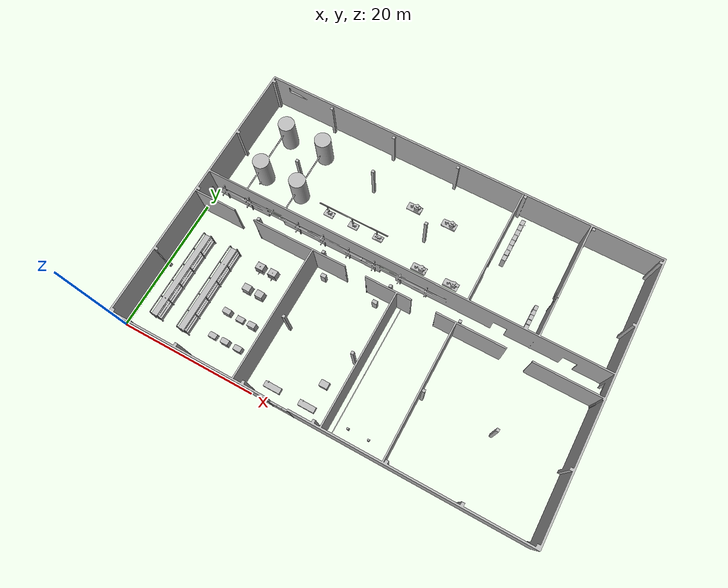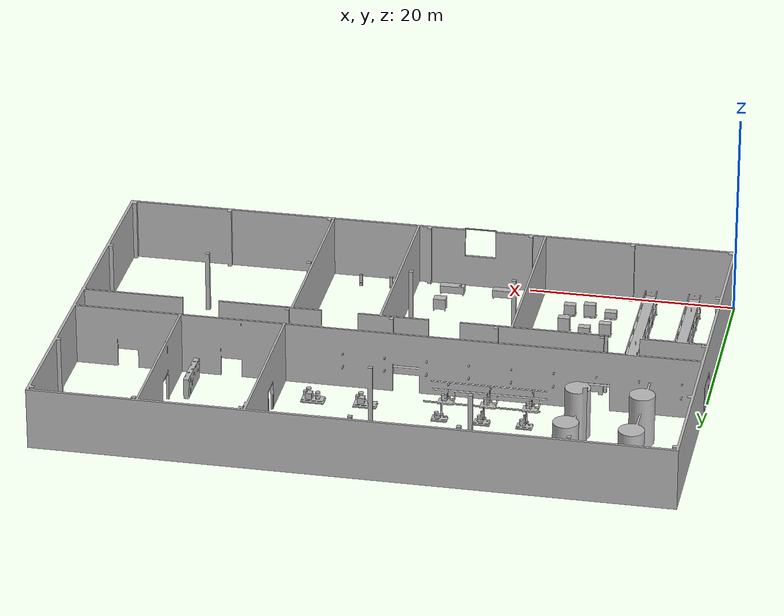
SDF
<?xml version="1.0" ?>
<sdf version="1.6">
  <model name="amr_inspection_facility">

    <!-- مهم جداً تخليها true عشان المصنع ميبقاش طاير ويقع أو يتحرك لما الروبوت يخبط فيه -->
    <static>true</static>

    <link name="factory_base_link">

      <!-- 1. الجزء البصري (Visual) -->
       <visual name="factory_visual">
        <pose>0 0 0 0 0 0</pose>
        <geometry>
          <mesh>
            <uri>model://amr_inspection_facility/meshes/inspection_facility_visual.obj</uri>
            <scale>1 1 1</scale>
          </mesh>
        </geometry>
      </visual>

      <!-- 2. جزء التصادم (Collision) -->
      <!-- انسخ الـ 5000 سطر بتوع مكعبات التصادم وحطهم هنا بالظبط -->

    <collision name="box_wall_1">
      <pose>33.5000 2.0000 0.6000 0.0000 -0.0000 0.0000</pose>
      <geometry>
        <box>
          <size>0.3000 0.2000 1.2000</size>
        </box>
      </geometry>
      <surface>
        <friction>
          <ode>
            <mu>0.5</mu>
            <mu2>0.5</mu2>
          </ode>
        </friction>
      </surface>
    </collision>

    <collision name="box_wall_2">
      <pose>36.5000 2.0000 0.6000 0.0000 -0.0000 0.0000</pose>
      <geometry>
        <box>
          <size>0.3000 0.2000 1.2000</size>
        </box>
      </geometry>
      <surface>
        <friction>
          <ode>
            <mu>0.5</mu>
            <mu2>0.5</mu2>
          </ode>
        </friction>
      </surface>
    </collision>

    <collision name="box_wall_3">
      <pose>33.5000 2.0000 0.6000 0.0000 -0.0000 0.0000</pose>
      <geometry>
        <box>
          <size>0.3000 0.2000 1.2000</size>
        </box>
      </geometry>
      <surface>
        <friction>
          <ode>
            <mu>0.5</mu>
            <mu2>0.5</mu2>
          </ode>
        </friction>
      </surface>
    </collision>

    <collision name="box_wall_4">
      <pose>33.5000 2.1500 0.1800 0.0000 -0.0000 0.0000</pose>
      <geometry>
        <box>
          <size>0.3000 0.0600 0.0400</size>
        </box>
      </geometry>
      <surface>
        <friction>
          <ode>
            <mu>0.5</mu>
            <mu2>0.5</mu2>
          </ode>
        </friction>
      </surface>
    </collision>

    <collision name="box_wall_5">
      <pose>33.5000 2.1500 0.3500 0.0000 -0.0000 0.0000</pose>
      <geometry>
        <box>
          <size>0.3000 0.0600 0.0400</size>
        </box>
      </geometry>
      <surface>
        <friction>
          <ode>
            <mu>0.5</mu>
            <mu2>0.5</mu2>
          </ode>
        </friction>
      </surface>
    </collision>

    <collision name="box_wall_6">
      <pose>36.5000 2.0000 0.6000 0.0000 -0.0000 0.0000</pose>
      <geometry>
        <box>
          <size>0.3000 0.2000 1.2000</size>
        </box>
      </geometry>
      <surface>
        <friction>
          <ode>
            <mu>0.5</mu>
            <mu2>0.5</mu2>
          </ode>
        </friction>
      </surface>
    </collision>

    <collision name="box_wall_7">
      <pose>36.5000 2.1500 0.1800 0.0000 -0.0000 0.0000</pose>
      <geometry>
        <box>
          <size>0.3000 0.0600 0.0400</size>
        </box>
      </geometry>
      <surface>
        <friction>
          <ode>
            <mu>0.5</mu>
            <mu2>0.5</mu2>
          </ode>
        </friction>
      </surface>
    </collision>

    <collision name="box_wall_8">
      <pose>36.5000 2.1500 0.3500 0.0000 -0.0000 0.0000</pose>
      <geometry>
        <box>
          <size>0.3000 0.0600 0.0400</size>
        </box>
      </geometry>
      <surface>
        <friction>
          <ode>
            <mu>0.5</mu>
            <mu2>0.5</mu2>
          </ode>
        </friction>
      </surface>
    </collision>

    <collision name="box_wall_9">
      <pose>22.2128 2.0000 0.4500 0.0000 -0.0000 0.0000</pose>
      <geometry>
        <box>
          <size>2.4000 0.8000 0.9500</size>
        </box>
      </geometry>
      <surface>
        <friction>
          <ode>
            <mu>0.5</mu>
            <mu2>0.5</mu2>
          </ode>
        </friction>
      </surface>
    </collision>

    <collision name="box_wall_10">
      <pose>31.1000 1.6500 0.4500 0.0000 -0.0000 0.0000</pose>
      <geometry>
        <box>
          <size>0.0600 0.0600 0.9000</size>
        </box>
      </geometry>
      <surface>
        <friction>
          <ode>
            <mu>0.5</mu>
            <mu2>0.5</mu2>
          </ode>
        </friction>
      </surface>
    </collision>

    <collision name="box_wall_11">
      <pose>31.1000 2.3500 0.4500 0.0000 -0.0000 0.0000</pose>
      <geometry>
        <box>
          <size>0.0600 0.0600 0.9000</size>
        </box>
      </geometry>
      <surface>
        <friction>
          <ode>
            <mu>0.5</mu>
            <mu2>0.5</mu2>
          </ode>
        </friction>
      </surface>
    </collision>

    <collision name="box_wall_12">
      <pose>20.5000 18.3000 0.9500 0.0000 -0.0000 0.0000</pose>
      <geometry>
        <box>
          <size>0.7000 0.5000 1.9000</size>
        </box>
      </geometry>
      <surface>
        <friction>
          <ode>
            <mu>0.5</mu>
            <mu2>0.5</mu2>
          </ode>
        </friction>
      </surface>
    </collision>

    <collision name="box_wall_13">
      <pose>20.8600 18.3000 0.9500 0.0000 -0.0000 0.0000</pose>
      <geometry>
        <box>
          <size>0.0200 0.4600 1.8600</size>
        </box>
      </geometry>
      <surface>
        <friction>
          <ode>
            <mu>0.5</mu>
            <mu2>0.5</mu2>
          </ode>
        </friction>
      </surface>
    </collision>

    <collision name="box_wall_14">
      <pose>28.5000 18.3000 0.9500 0.0000 -0.0000 0.0000</pose>
      <geometry>
        <box>
          <size>0.7000 0.5000 1.9000</size>
        </box>
      </geometry>
      <surface>
        <friction>
          <ode>
            <mu>0.5</mu>
            <mu2>0.5</mu2>
          </ode>
        </friction>
      </surface>
    </collision>

    <collision name="box_wall_15">
      <pose>28.8600 18.3000 0.9500 0.0000 -0.0000 0.0000</pose>
      <geometry>
        <box>
          <size>0.0200 0.4600 1.8600</size>
        </box>
      </geometry>
      <surface>
        <friction>
          <ode>
            <mu>0.5</mu>
            <mu2>0.5</mu2>
          </ode>
        </friction>
      </surface>
    </collision>

    <collision name="box_wall_16">
      <pose>28.0000 5.5000 0.8500 0.0000 -0.0000 0.0000</pose>
      <geometry>
        <box>
          <size>1.2000 0.9000 0.8000</size>
        </box>
      </geometry>
      <surface>
        <friction>
          <ode>
            <mu>0.5</mu>
            <mu2>0.5</mu2>
          </ode>
        </friction>
      </surface>
    </collision>

    <collision name="box_wall_17">
      <pose>27.4500 5.1000 0.4000 0.0000 -0.0000 0.0000</pose>
      <geometry>
        <box>
          <size>0.0600 0.0600 0.8000</size>
        </box>
      </geometry>
      <surface>
        <friction>
          <ode>
            <mu>0.5</mu>
            <mu2>0.5</mu2>
          </ode>
        </friction>
      </surface>
    </collision>

    <collision name="box_wall_18">
      <pose>27.4500 5.9000 0.4000 0.0000 -0.0000 0.0000</pose>
      <geometry>
        <box>
          <size>0.0600 0.0600 0.8000</size>
        </box>
      </geometry>
      <surface>
        <friction>
          <ode>
            <mu>0.5</mu>
            <mu2>0.5</mu2>
          </ode>
        </friction>
      </surface>
    </collision>

    <collision name="box_wall_19">
      <pose>28.5500 5.1000 0.4000 0.0000 -0.0000 0.0000</pose>
      <geometry>
        <box>
          <size>0.0600 0.0600 0.8000</size>
        </box>
      </geometry>
      <surface>
        <friction>
          <ode>
            <mu>0.5</mu>
            <mu2>0.5</mu2>
          </ode>
        </friction>
      </surface>
    </collision>

    <collision name="box_wall_20">
      <pose>28.5500 5.9000 0.4000 0.0000 -0.0000 0.0000</pose>
      <geometry>
        <box>
          <size>0.0600 0.0600 0.8000</size>
        </box>
      </geometry>
      <surface>
        <friction>
          <ode>
            <mu>0.5</mu>
            <mu2>0.5</mu2>
          </ode>
        </friction>
      </surface>
    </collision>

    <collision name="box_wall_21">
      <pose>18.0000 22.4500 2.5000 0.0000 -0.0000 0.0000</pose>
      <geometry>
        <box>
          <size>0.1600 0.0500 0.1600</size>
        </box>
      </geometry>
      <surface>
        <friction>
          <ode>
            <mu>0.5</mu>
            <mu2>0.5</mu2>
          </ode>
        </friction>
      </surface>
    </collision>

    <collision name="box_wall_22">
      <pose>18.0000 22.4240 2.5000 0.0000 -0.0000 0.0000</pose>
      <geometry>
        <box>
          <size>0.1400 0.1400 0.0050</size>
        </box>
      </geometry>
      <surface>
        <friction>
          <ode>
            <mu>0.5</mu>
            <mu2>0.5</mu2>
          </ode>
        </friction>
      </surface>
    </collision>

    <collision name="box_wall_23">
      <pose>18.2000 22.4500 2.5000 0.0000 -0.0000 0.0000</pose>
      <geometry>
        <box>
          <size>0.1500 0.0075 0.1500</size>
        </box>
      </geometry>
      <surface>
        <friction>
          <ode>
            <mu>0.5</mu>
            <mu2>0.5</mu2>
          </ode>
        </friction>
      </surface>
    </collision>

    <collision name="box_wall_24">
      <pose>11.7500 0.1250 3.1391 0.0000 -0.0000 0.0000</pose>
      <geometry>
        <box>
          <size>23.5000 0.2500 6.0000</size>
        </box>
      </geometry>
      <surface>
        <friction>
          <ode>
            <mu>0.5</mu>
            <mu2>0.5</mu2>
          </ode>
        </friction>
      </surface>
    </collision>

    <collision name="box_wall_25">
      <pose>25.0000 0.1250 1.7257 0.0000 -0.0000 0.0000</pose>
      <geometry>
        <box>
          <size>3.0000 0.2500 3.2000</size>
        </box>
      </geometry>
      <surface>
        <friction>
          <ode>
            <mu>0.5</mu>
            <mu2>0.5</mu2>
          </ode>
        </friction>
      </surface>
    </collision>

    <collision name="box_wall_26">
      <pose>43.2500 0.1250 3.1391 0.0000 -0.0000 0.0000</pose>
      <geometry>
        <box>
          <size>33.5000 0.2500 6.0000</size>
        </box>
      </geometry>
      <surface>
        <friction>
          <ode>
            <mu>0.5</mu>
            <mu2>0.5</mu2>
          </ode>
        </friction>
      </surface>
    </collision>

    <collision name="box_wall_27">
      <pose>30.0000 40.1887 3.1391 0.0000 -0.0000 0.0000</pose>
      <geometry>
        <box>
          <size>60.0000 0.2500 6.0000</size>
        </box>
      </geometry>
      <surface>
        <friction>
          <ode>
            <mu>0.5</mu>
            <mu2>0.5</mu2>
          </ode>
        </friction>
      </surface>
    </collision>

    <collision name="box_wall_28">
      <pose>0.1250 9.6250 3.1391 0.0000 -0.0000 0.0000</pose>
      <geometry>
        <box>
          <size>0.2500 19.2500 6.0000</size>
        </box>
      </geometry>
      <surface>
        <friction>
          <ode>
            <mu>0.5</mu>
            <mu2>0.5</mu2>
          </ode>
        </friction>
      </surface>
    </collision>

    <collision name="box_wall_29">
      <pose>0.1250 20.7500 4.5391 0.0000 -0.0000 0.0000</pose>
      <geometry>
        <box>
          <size>0.2500 3.0000 3.2000</size>
        </box>
      </geometry>
      <surface>
        <friction>
          <ode>
            <mu>0.5</mu>
            <mu2>0.5</mu2>
          </ode>
        </friction>
      </surface>
    </collision>

    <collision name="box_wall_30">
      <pose>0.1250 31.1750 3.1391 0.0000 -0.0000 0.0000</pose>
      <geometry>
        <box>
          <size>0.2500 17.8500 6.0000</size>
        </box>
      </geometry>
      <surface>
        <friction>
          <ode>
            <mu>0.5</mu>
            <mu2>0.5</mu2>
          </ode>
        </friction>
      </surface>
    </collision>

    <collision name="box_wall_31">
      <pose>59.8750 9.6250 3.1391 0.0000 -0.0000 0.0000</pose>
      <geometry>
        <box>
          <size>0.2500 19.2500 6.0000</size>
        </box>
      </geometry>
      <surface>
        <friction>
          <ode>
            <mu>0.5</mu>
            <mu2>0.5</mu2>
          </ode>
        </friction>
      </surface>
    </collision>

    <collision name="box_wall_32">
      <pose>59.8750 20.7500 4.5391 0.0000 -0.0000 0.0000</pose>
      <geometry>
        <box>
          <size>0.2500 3.0000 3.2000</size>
        </box>
      </geometry>
      <surface>
        <friction>
          <ode>
            <mu>0.5</mu>
            <mu2>0.5</mu2>
          </ode>
        </friction>
      </surface>
    </collision>

    <collision name="box_wall_33">
      <pose>59.8750 31.1250 3.1391 0.0000 -0.0000 0.0000</pose>
      <geometry>
        <box>
          <size>0.2500 17.7500 6.0000</size>
        </box>
      </geometry>
      <surface>
        <friction>
          <ode>
            <mu>0.5</mu>
            <mu2>0.5</mu2>
          </ode>
        </friction>
      </surface>
    </collision>

    <collision name="box_wall_34">
      <pose>3.3750 19.6000 3.1391 0.0000 -0.0000 0.0000</pose>
      <geometry>
        <box>
          <size>6.2500 0.2000 6.0000</size>
        </box>
      </geometry>
      <surface>
        <friction>
          <ode>
            <mu>0.5</mu>
            <mu2>0.5</mu2>
          </ode>
        </friction>
      </surface>
    </collision>

    <collision name="box_wall_35">
      <pose>16.5000 19.6000 3.1391 0.0000 -0.0000 0.0000</pose>
      <geometry>
        <box>
          <size>14.0000 0.2000 6.0000</size>
        </box>
      </geometry>
      <surface>
        <friction>
          <ode>
            <mu>0.5</mu>
            <mu2>0.5</mu2>
          </ode>
        </friction>
      </surface>
    </collision>

    <collision name="box_wall_36">
      <pose>54.9600 19.6000 3.1391 0.0000 -0.0000 0.0000</pose>
      <geometry>
        <box>
          <size>9.5800 0.2000 6.0000</size>
        </box>
      </geometry>
      <surface>
        <friction>
          <ode>
            <mu>0.5</mu>
            <mu2>0.5</mu2>
          </ode>
        </friction>
      </surface>
    </collision>

    <collision name="box_wall_37">
      <pose>4.5000 23.0000 3.1391 0.0000 -0.0000 0.0000</pose>
      <geometry>
        <box>
          <size>8.5000 0.2000 6.0000</size>
        </box>
      </geometry>
      <surface>
        <friction>
          <ode>
            <mu>0.5</mu>
            <mu2>0.5</mu2>
          </ode>
        </friction>
      </surface>
    </collision>

    <collision name="box_wall_38">
      <pose>19.0000 23.0000 3.1391 0.0000 -0.0000 0.0000</pose>
      <geometry>
        <box>
          <size>15.5000 0.2000 6.0000</size>
        </box>
      </geometry>
      <surface>
        <friction>
          <ode>
            <mu>0.5</mu>
            <mu2>0.5</mu2>
          </ode>
        </friction>
      </surface>
    </collision>

    <collision name="box_wall_39">
      <pose>34.3750 23.0000 3.1391 0.0000 -0.0000 0.0000</pose>
      <geometry>
        <box>
          <size>10.2500 0.2000 6.0000</size>
        </box>
      </geometry>
      <surface>
        <friction>
          <ode>
            <mu>0.5</mu>
            <mu2>0.5</mu2>
          </ode>
        </friction>
      </surface>
    </collision>

    <collision name="box_wall_40">
      <pose>10.0000 23.0000 4.5391 0.0000 -0.0000 0.0000</pose>
      <geometry>
        <box>
          <size>2.5000 0.2000 3.2000</size>
        </box>
      </geometry>
      <surface>
        <friction>
          <ode>
            <mu>0.5</mu>
            <mu2>0.5</mu2>
          </ode>
        </friction>
      </surface>
    </collision>

    <collision name="box_wall_41">
      <pose>28.0000 23.0000 4.5391 0.0000 -0.0000 0.0000</pose>
      <geometry>
        <box>
          <size>2.5000 0.2000 3.2000</size>
        </box>
      </geometry>
      <surface>
        <friction>
          <ode>
            <mu>0.5</mu>
            <mu2>0.5</mu2>
          </ode>
        </friction>
      </surface>
    </collision>

    <collision name="box_wall_42">
      <pose>39.6000 25.9391 3.1391 0.0000 -0.0000 0.0000</pose>
      <geometry>
        <box>
          <size>0.2000 5.8000 6.0000</size>
        </box>
      </geometry>
      <surface>
        <friction>
          <ode>
            <mu>0.5</mu>
            <mu2>0.5</mu2>
          </ode>
        </friction>
      </surface>
    </collision>

    <collision name="box_wall_43">
      <pose>39.6000 29.7500 4.5391 0.0000 -0.0000 0.0000</pose>
      <geometry>
        <box>
          <size>0.2000 2.0000 3.2000</size>
        </box>
      </geometry>
      <surface>
        <friction>
          <ode>
            <mu>0.5</mu>
            <mu2>0.5</mu2>
          </ode>
        </friction>
      </surface>
    </collision>

    <collision name="box_wall_44">
      <pose>39.6000 35.4000 3.1391 0.0000 -0.0000 0.0000</pose>
      <geometry>
        <box>
          <size>0.2000 9.3000 6.0000</size>
        </box>
      </geometry>
      <surface>
        <friction>
          <ode>
            <mu>0.5</mu>
            <mu2>0.5</mu2>
          </ode>
        </friction>
      </surface>
    </collision>

    <collision name="box_wall_45">
      <pose>49.6000 25.7791 3.1391 0.0000 -0.0000 0.0000</pose>
      <geometry>
        <box>
          <size>0.2000 5.8000 6.0000</size>
        </box>
      </geometry>
      <surface>
        <friction>
          <ode>
            <mu>0.5</mu>
            <mu2>0.5</mu2>
          </ode>
        </friction>
      </surface>
    </collision>

    <collision name="box_wall_46">
      <pose>49.6000 29.6500 4.5391 0.0000 -0.0000 0.0000</pose>
      <geometry>
        <box>
          <size>0.2000 1.8000 3.2000</size>
        </box>
      </geometry>
      <surface>
        <friction>
          <ode>
            <mu>0.5</mu>
            <mu2>0.5</mu2>
          </ode>
        </friction>
      </surface>
    </collision>

    <collision name="box_wall_47">
      <pose>49.6000 35.4000 3.1391 0.0000 -0.0000 0.0000</pose>
      <geometry>
        <box>
          <size>0.2000 9.3000 6.0000</size>
        </box>
      </geometry>
      <surface>
        <friction>
          <ode>
            <mu>0.5</mu>
            <mu2>0.5</mu2>
          </ode>
        </friction>
      </surface>
    </collision>

    <collision name="box_wall_48">
      <pose>41.6250 22.9849 3.1391 0.0000 -0.0000 0.0000</pose>
      <geometry>
        <box>
          <size>4.2500 0.2000 6.0000</size>
        </box>
      </geometry>
      <surface>
        <friction>
          <ode>
            <mu>0.5</mu>
            <mu2>0.5</mu2>
          </ode>
        </friction>
      </surface>
    </collision>

    <collision name="box_wall_49">
      <pose>44.7500 23.0000 4.5391 0.0000 -0.0000 0.0000</pose>
      <geometry>
        <box>
          <size>2.0000 0.2000 3.2000</size>
        </box>
      </geometry>
      <surface>
        <friction>
          <ode>
            <mu>0.5</mu>
            <mu2>0.5</mu2>
          </ode>
        </friction>
      </surface>
    </collision>

    <collision name="box_wall_50">
      <pose>47.6250 23.0000 3.1391 0.0000 -0.0000 0.0000</pose>
      <geometry>
        <box>
          <size>3.7500 0.2000 6.0000</size>
        </box>
      </geometry>
      <surface>
        <friction>
          <ode>
            <mu>0.5</mu>
            <mu2>0.5</mu2>
          </ode>
        </friction>
      </surface>
    </collision>

    <collision name="box_wall_51">
      <pose>51.6250 23.0000 3.1391 0.0000 -0.0000 0.0000</pose>
      <geometry>
        <box>
          <size>4.2500 0.2000 6.0000</size>
        </box>
      </geometry>
      <surface>
        <friction>
          <ode>
            <mu>0.5</mu>
            <mu2>0.5</mu2>
          </ode>
        </friction>
      </surface>
    </collision>

    <collision name="box_wall_52">
      <pose>54.7500 23.0000 4.5391 0.0000 -0.0000 0.0000</pose>
      <geometry>
        <box>
          <size>2.0000 0.2000 3.2000</size>
        </box>
      </geometry>
      <surface>
        <friction>
          <ode>
            <mu>0.5</mu>
            <mu2>0.5</mu2>
          </ode>
        </friction>
      </surface>
    </collision>

    <collision name="box_wall_53">
      <pose>57.7500 23.0000 3.1391 0.0000 -0.0000 0.0000</pose>
      <geometry>
        <box>
          <size>4.0000 0.2000 6.0000</size>
        </box>
      </geometry>
      <surface>
        <friction>
          <ode>
            <mu>0.5</mu>
            <mu2>0.5</mu2>
          </ode>
        </friction>
      </surface>
    </collision>

    <collision name="box_wall_54">
      <pose>18.6000 9.8750 3.1391 0.0000 -0.0000 0.0000</pose>
      <geometry>
        <box>
          <size>0.2000 19.2500 6.0000</size>
        </box>
      </geometry>
      <surface>
        <friction>
          <ode>
            <mu>0.5</mu>
            <mu2>0.5</mu2>
          </ode>
        </friction>
      </surface>
    </collision>

    <collision name="box_wall_55">
      <pose>31.1000 9.8750 3.1391 0.0000 -0.0000 0.0000</pose>
      <geometry>
        <box>
          <size>0.2000 19.2500 6.0000</size>
        </box>
      </geometry>
      <surface>
        <friction>
          <ode>
            <mu>0.5</mu>
            <mu2>0.5</mu2>
          </ode>
        </friction>
      </surface>
    </collision>

    <collision name="box_wall_56">
      <pose>39.6000 9.8750 3.1391 0.0000 -0.0000 0.0000</pose>
      <geometry>
        <box>
          <size>0.2000 19.2500 6.0000</size>
        </box>
      </geometry>
      <surface>
        <friction>
          <ode>
            <mu>0.5</mu>
            <mu2>0.5</mu2>
          </ode>
        </friction>
      </surface>
    </collision>

    <collision name="box_wall_57">
      <pose>29.8750 19.6000 3.1391 0.0000 -0.0000 0.0000</pose>
      <geometry>
        <box>
          <size>6.7500 0.2000 6.0000</size>
        </box>
      </geometry>
      <surface>
        <friction>
          <ode>
            <mu>0.5</mu>
            <mu2>0.5</mu2>
          </ode>
        </friction>
      </surface>
    </collision>

    <collision name="box_wall_58">
      <pose>10.0000 23.0000 2.9791 0.0000 -0.0000 0.0000</pose>
      <geometry>
        <box>
          <size>2.6600 0.1200 0.0800</size>
        </box>
      </geometry>
      <surface>
        <friction>
          <ode>
            <mu>0.5</mu>
            <mu2>0.5</mu2>
          </ode>
        </friction>
      </surface>
    </collision>

    <collision name="box_wall_59">
      <pose>8.7100 23.0000 1.5391 0.0000 -0.0000 0.0000</pose>
      <geometry>
        <box>
          <size>0.0800 0.1200 2.8000</size>
        </box>
      </geometry>
      <surface>
        <friction>
          <ode>
            <mu>0.5</mu>
            <mu2>0.5</mu2>
          </ode>
        </friction>
      </surface>
    </collision>

    <collision name="box_wall_60">
      <pose>11.2900 23.0000 1.5391 0.0000 -0.0000 0.0000</pose>
      <geometry>
        <box>
          <size>0.0800 0.1200 2.8000</size>
        </box>
      </geometry>
      <surface>
        <friction>
          <ode>
            <mu>0.5</mu>
            <mu2>0.5</mu2>
          </ode>
        </friction>
      </surface>
    </collision>

    <collision name="box_wall_61">
      <pose>28.0000 23.0000 2.9791 0.0000 -0.0000 0.0000</pose>
      <geometry>
        <box>
          <size>2.6600 0.1200 0.0800</size>
        </box>
      </geometry>
      <surface>
        <friction>
          <ode>
            <mu>0.5</mu>
            <mu2>0.5</mu2>
          </ode>
        </friction>
      </surface>
    </collision>

    <collision name="box_wall_62">
      <pose>26.7100 23.0000 1.5391 0.0000 -0.0000 0.0000</pose>
      <geometry>
        <box>
          <size>0.0800 0.1200 2.8000</size>
        </box>
      </geometry>
      <surface>
        <friction>
          <ode>
            <mu>0.5</mu>
            <mu2>0.5</mu2>
          </ode>
        </friction>
      </surface>
    </collision>

    <collision name="box_wall_63">
      <pose>29.2900 23.0000 1.5391 0.0000 -0.0000 0.0000</pose>
      <geometry>
        <box>
          <size>0.0800 0.1200 2.8000</size>
        </box>
      </geometry>
      <surface>
        <friction>
          <ode>
            <mu>0.5</mu>
            <mu2>0.5</mu2>
          </ode>
        </friction>
      </surface>
    </collision>

    <collision name="box_wall_64">
      <pose>39.5000 29.7500 2.9791 0.0000 -0.0000 0.0000</pose>
      <geometry>
        <box>
          <size>0.1200 2.1600 0.0800</size>
        </box>
      </geometry>
      <surface>
        <friction>
          <ode>
            <mu>0.5</mu>
            <mu2>0.5</mu2>
          </ode>
        </friction>
      </surface>
    </collision>

    <collision name="box_wall_65">
      <pose>39.5000 28.7100 1.5391 0.0000 -0.0000 0.0000</pose>
      <geometry>
        <box>
          <size>0.1200 0.0800 2.8000</size>
        </box>
      </geometry>
      <surface>
        <friction>
          <ode>
            <mu>0.5</mu>
            <mu2>0.5</mu2>
          </ode>
        </friction>
      </surface>
    </collision>

    <collision name="box_wall_66">
      <pose>39.5000 30.7900 1.5391 0.0000 -0.0000 0.0000</pose>
      <geometry>
        <box>
          <size>0.1200 0.0800 2.8000</size>
        </box>
      </geometry>
      <surface>
        <friction>
          <ode>
            <mu>0.5</mu>
            <mu2>0.5</mu2>
          </ode>
        </friction>
      </surface>
    </collision>

    <collision name="box_wall_67">
      <pose>44.7500 23.0000 2.9791 0.0000 -0.0000 0.0000</pose>
      <geometry>
        <box>
          <size>2.1600 0.1200 0.0800</size>
        </box>
      </geometry>
      <surface>
        <friction>
          <ode>
            <mu>0.5</mu>
            <mu2>0.5</mu2>
          </ode>
        </friction>
      </surface>
    </collision>

    <collision name="box_wall_68">
      <pose>43.7100 23.0000 1.5391 0.0000 -0.0000 0.0000</pose>
      <geometry>
        <box>
          <size>0.0800 0.1200 2.8000</size>
        </box>
      </geometry>
      <surface>
        <friction>
          <ode>
            <mu>0.5</mu>
            <mu2>0.5</mu2>
          </ode>
        </friction>
      </surface>
    </collision>

    <collision name="box_wall_69">
      <pose>45.7900 23.0000 1.5391 0.0000 -0.0000 0.0000</pose>
      <geometry>
        <box>
          <size>0.0800 0.1200 2.8000</size>
        </box>
      </geometry>
      <surface>
        <friction>
          <ode>
            <mu>0.5</mu>
            <mu2>0.5</mu2>
          </ode>
        </friction>
      </surface>
    </collision>

    <collision name="box_wall_70">
      <pose>49.5000 29.6500 2.9791 0.0000 -0.0000 0.0000</pose>
      <geometry>
        <box>
          <size>0.1200 1.9600 0.0800</size>
        </box>
      </geometry>
      <surface>
        <friction>
          <ode>
            <mu>0.5</mu>
            <mu2>0.5</mu2>
          </ode>
        </friction>
      </surface>
    </collision>

    <collision name="box_wall_71">
      <pose>49.5000 28.7100 1.5391 0.0000 -0.0000 0.0000</pose>
      <geometry>
        <box>
          <size>0.1200 0.0800 2.8000</size>
        </box>
      </geometry>
      <surface>
        <friction>
          <ode>
            <mu>0.5</mu>
            <mu2>0.5</mu2>
          </ode>
        </friction>
      </surface>
    </collision>

    <collision name="box_wall_73">
      <pose>54.7500 23.0000 2.9791 0.0000 -0.0000 0.0000</pose>
      <geometry>
        <box>
          <size>2.1600 0.1200 0.0800</size>
        </box>
      </geometry>
      <surface>
        <friction>
          <ode>
            <mu>0.5</mu>
            <mu2>0.5</mu2>
          </ode>
        </friction>
      </surface>
    </collision>

    <collision name="box_wall_74">
      <pose>53.7100 23.0000 1.5391 0.0000 -0.0000 0.0000</pose>
      <geometry>
        <box>
          <size>0.0800 0.1200 2.8000</size>
        </box>
      </geometry>
      <surface>
        <friction>
          <ode>
            <mu>0.5</mu>
            <mu2>0.5</mu2>
          </ode>
        </friction>
      </surface>
    </collision>

    <collision name="box_wall_75">
      <pose>55.7900 23.0000 1.5391 0.0000 -0.0000 0.0000</pose>
      <geometry>
        <box>
          <size>0.0800 0.1200 2.8000</size>
        </box>
      </geometry>
      <surface>
        <friction>
          <ode>
            <mu>0.5</mu>
            <mu2>0.5</mu2>
          </ode>
        </friction>
      </surface>
    </collision>

    <collision name="box_wall_76">
      <pose>23.4600 19.5000 1.5391 0.0000 -0.0000 0.0000</pose>
      <geometry>
        <box>
          <size>0.0800 0.1200 2.8000</size>
        </box>
      </geometry>
      <surface>
        <friction>
          <ode>
            <mu>0.5</mu>
            <mu2>0.5</mu2>
          </ode>
        </friction>
      </surface>
    </collision>

    <collision name="box_wall_77">
      <pose>26.5400 19.5000 1.5391 0.0000 -0.0000 0.0000</pose>
      <geometry>
        <box>
          <size>0.0800 0.1200 2.8000</size>
        </box>
      </geometry>
      <surface>
        <friction>
          <ode>
            <mu>0.5</mu>
            <mu2>0.5</mu2>
          </ode>
        </friction>
      </surface>
    </collision>

    <collision name="box_wall_78">
      <pose>25.0000 0.0000 6.1791 0.0000 -0.0000 0.0000</pose>
      <geometry>
        <box>
          <size>3.1600 0.1200 0.0800</size>
        </box>
      </geometry>
      <surface>
        <friction>
          <ode>
            <mu>0.5</mu>
            <mu2>0.5</mu2>
          </ode>
        </friction>
      </surface>
    </collision>

    <collision name="box_wall_79">
      <pose>23.4600 0.0000 3.1391 0.0000 -0.0000 0.0000</pose>
      <geometry>
        <box>
          <size>0.0800 0.1200 6.0000</size>
        </box>
      </geometry>
      <surface>
        <friction>
          <ode>
            <mu>0.5</mu>
            <mu2>0.5</mu2>
          </ode>
        </friction>
      </surface>
    </collision>

    <collision name="box_wall_80">
      <pose>26.5400 0.0000 3.1391 0.0000 -0.0000 0.0000</pose>
      <geometry>
        <box>
          <size>0.0800 0.1200 6.0000</size>
        </box>
      </geometry>
      <surface>
        <friction>
          <ode>
            <mu>0.5</mu>
            <mu2>0.5</mu2>
          </ode>
        </friction>
      </surface>
    </collision>

    <collision name="box_wall_81">
      <pose>33.2100 19.5000 1.5391 0.0000 -0.0000 0.0000</pose>
      <geometry>
        <box>
          <size>0.0800 0.1200 2.8000</size>
        </box>
      </geometry>
      <surface>
        <friction>
          <ode>
            <mu>0.5</mu>
            <mu2>0.5</mu2>
          </ode>
        </friction>
      </surface>
    </collision>

    <collision name="box_wall_82">
      <pose>36.7900 19.5000 1.5391 0.0000 -0.0000 0.0000</pose>
      <geometry>
        <box>
          <size>0.0800 0.1200 2.8000</size>
        </box>
      </geometry>
      <surface>
        <friction>
          <ode>
            <mu>0.5</mu>
            <mu2>0.5</mu2>
          </ode>
        </friction>
      </surface>
    </collision>

    <collision name="box_wall_83">
      <pose>59.7500 20.7500 2.9791 0.0000 -0.0000 0.0000</pose>
      <geometry>
        <box>
          <size>0.1200 3.1600 0.0800</size>
        </box>
      </geometry>
      <surface>
        <friction>
          <ode>
            <mu>0.5</mu>
            <mu2>0.5</mu2>
          </ode>
        </friction>
      </surface>
    </collision>

    <collision name="box_wall_84">
      <pose>59.7500 19.2100 1.5391 0.0000 -0.0000 0.0000</pose>
      <geometry>
        <box>
          <size>0.1200 0.0800 2.8000</size>
        </box>
      </geometry>
      <surface>
        <friction>
          <ode>
            <mu>0.5</mu>
            <mu2>0.5</mu2>
          </ode>
        </friction>
      </surface>
    </collision>

    <collision name="box_wall_85">
      <pose>59.7500 22.2900 1.5391 0.0000 -0.0000 0.0000</pose>
      <geometry>
        <box>
          <size>0.1200 0.0800 2.8000</size>
        </box>
      </geometry>
      <surface>
        <friction>
          <ode>
            <mu>0.5</mu>
            <mu2>0.5</mu2>
          </ode>
        </friction>
      </surface>
    </collision>

    <collision name="box_wall_86">
      <pose>-0.0000 20.7500 2.9791 0.0000 -0.0000 0.0000</pose>
      <geometry>
        <box>
          <size>0.1200 3.1600 0.0800</size>
        </box>
      </geometry>
      <surface>
        <friction>
          <ode>
            <mu>0.5</mu>
            <mu2>0.5</mu2>
          </ode>
        </friction>
      </surface>
    </collision>

    <collision name="box_wall_87">
      <pose>-0.0000 19.2100 1.5391 0.0000 -0.0000 0.0000</pose>
      <geometry>
        <box>
          <size>0.1200 0.0800 2.8000</size>
        </box>
      </geometry>
      <surface>
        <friction>
          <ode>
            <mu>0.5</mu>
            <mu2>0.5</mu2>
          </ode>
        </friction>
      </surface>
    </collision>

    <collision name="box_wall_88">
      <pose>-0.0000 22.2900 1.5391 0.0000 -0.0000 0.0000</pose>
      <geometry>
        <box>
          <size>0.1200 0.0800 2.8000</size>
        </box>
      </geometry>
      <surface>
        <friction>
          <ode>
            <mu>0.5</mu>
            <mu2>0.5</mu2>
          </ode>
        </friction>
      </surface>
    </collision>

    <collision name="box_wall_89">
      <pose>-0.0000 20.7500 1.5391 0.0000 -0.0000 0.0000</pose>
      <geometry>
        <box>
          <size>0.0500 2.9800 2.7800</size>
        </box>
      </geometry>
      <surface>
        <friction>
          <ode>
            <mu>0.5</mu>
            <mu2>0.5</mu2>
          </ode>
        </friction>
      </surface>
    </collision>

    <collision name="box_wall_90">
      <pose>0.4500 0.4500 3.1391 0.0000 -0.0000 0.0000</pose>
      <geometry>
        <box>
          <size>0.4000 0.4000 6.0000</size>
        </box>
      </geometry>
      <surface>
        <friction>
          <ode>
            <mu>0.5</mu>
            <mu2>0.5</mu2>
          </ode>
        </friction>
      </surface>
    </collision>

    <collision name="box_wall_91">
      <pose>0.4500 10.0000 3.1391 0.0000 -0.0000 0.0000</pose>
      <geometry>
        <box>
          <size>0.4000 0.4000 6.0000</size>
        </box>
      </geometry>
      <surface>
        <friction>
          <ode>
            <mu>0.5</mu>
            <mu2>0.5</mu2>
          </ode>
        </friction>
      </surface>
    </collision>

    <collision name="box_wall_92">
      <pose>0.4500 20.0000 3.1391 0.0000 -0.0000 0.0000</pose>
      <geometry>
        <box>
          <size>0.4000 0.4000 6.0000</size>
        </box>
      </geometry>
      <surface>
        <friction>
          <ode>
            <mu>0.5</mu>
            <mu2>0.5</mu2>
          </ode>
        </friction>
      </surface>
    </collision>

    <collision name="box_wall_93">
      <pose>0.4500 30.0000 3.1391 0.0000 -0.0000 0.0000</pose>
      <geometry>
        <box>
          <size>0.4000 0.4000 6.0000</size>
        </box>
      </geometry>
      <surface>
        <friction>
          <ode>
            <mu>0.5</mu>
            <mu2>0.5</mu2>
          </ode>
        </friction>
      </surface>
    </collision>

    <collision name="box_wall_94">
      <pose>0.4500 39.5500 3.1391 0.0000 -0.0000 0.0000</pose>
      <geometry>
        <box>
          <size>0.4000 0.4000 6.0000</size>
        </box>
      </geometry>
      <surface>
        <friction>
          <ode>
            <mu>0.5</mu>
            <mu2>0.5</mu2>
          </ode>
        </friction>
      </surface>
    </collision>

    <collision name="box_wall_95">
      <pose>10.0000 0.4500 3.1391 0.0000 -0.0000 0.0000</pose>
      <geometry>
        <box>
          <size>0.4000 0.4000 6.0000</size>
        </box>
      </geometry>
      <surface>
        <friction>
          <ode>
            <mu>0.5</mu>
            <mu2>0.5</mu2>
          </ode>
        </friction>
      </surface>
    </collision>

    <collision name="box_wall_96">
      <pose>10.0000 20.0000 3.1391 0.0000 -0.0000 0.0000</pose>
      <geometry>
        <box>
          <size>0.4000 0.4000 6.0000</size>
        </box>
      </geometry>
      <surface>
        <friction>
          <ode>
            <mu>0.5</mu>
            <mu2>0.5</mu2>
          </ode>
        </friction>
      </surface>
    </collision>

    <collision name="box_wall_97">
      <pose>10.0000 30.0000 3.1391 0.0000 -0.0000 0.0000</pose>
      <geometry>
        <box>
          <size>0.4000 0.4000 6.0000</size>
        </box>
      </geometry>
      <surface>
        <friction>
          <ode>
            <mu>0.5</mu>
            <mu2>0.5</mu2>
          </ode>
        </friction>
      </surface>
    </collision>

    <collision name="box_wall_98">
      <pose>10.0000 39.5500 3.1391 0.0000 -0.0000 0.0000</pose>
      <geometry>
        <box>
          <size>0.4000 0.4000 6.0000</size>
        </box>
      </geometry>
      <surface>
        <friction>
          <ode>
            <mu>0.5</mu>
            <mu2>0.5</mu2>
          </ode>
        </friction>
      </surface>
    </collision>

    <collision name="box_wall_99">
      <pose>20.0000 0.4500 3.1391 0.0000 -0.0000 0.0000</pose>
      <geometry>
        <box>
          <size>0.4000 0.4000 6.0000</size>
        </box>
      </geometry>
      <surface>
        <friction>
          <ode>
            <mu>0.5</mu>
            <mu2>0.5</mu2>
          </ode>
        </friction>
      </surface>
    </collision>

    <collision name="box_wall_100">
      <pose>20.0000 10.0000 3.1391 0.0000 -0.0000 0.0000</pose>
      <geometry>
        <box>
          <size>0.4000 0.4000 6.0000</size>
        </box>
      </geometry>
      <surface>
        <friction>
          <ode>
            <mu>0.5</mu>
            <mu2>0.5</mu2>
          </ode>
        </friction>
      </surface>
    </collision>

    <collision name="box_wall_101">
      <pose>20.0000 20.0000 3.1391 0.0000 -0.0000 0.0000</pose>
      <geometry>
        <box>
          <size>0.4000 0.4000 6.0000</size>
        </box>
      </geometry>
      <surface>
        <friction>
          <ode>
            <mu>0.5</mu>
            <mu2>0.5</mu2>
          </ode>
        </friction>
      </surface>
    </collision>

    <collision name="box_wall_102">
      <pose>20.0000 33.5119 3.1391 0.0000 -0.0000 0.0000</pose>
      <geometry>
        <box>
          <size>0.4000 0.4000 6.0000</size>
        </box>
      </geometry>
      <surface>
        <friction>
          <ode>
            <mu>0.5</mu>
            <mu2>0.5</mu2>
          </ode>
        </friction>
      </surface>
    </collision>

    <collision name="box_wall_103">
      <pose>20.0000 39.5500 3.1391 0.0000 -0.0000 0.0000</pose>
      <geometry>
        <box>
          <size>0.4000 0.4000 6.0000</size>
        </box>
      </geometry>
      <surface>
        <friction>
          <ode>
            <mu>0.5</mu>
            <mu2>0.5</mu2>
          </ode>
        </friction>
      </surface>
    </collision>

    <collision name="box_wall_104">
      <pose>30.0000 0.4500 3.1391 0.0000 -0.0000 0.0000</pose>
      <geometry>
        <box>
          <size>0.4000 0.4000 6.0000</size>
        </box>
      </geometry>
      <surface>
        <friction>
          <ode>
            <mu>0.5</mu>
            <mu2>0.5</mu2>
          </ode>
        </friction>
      </surface>
    </collision>

    <collision name="box_wall_105">
      <pose>30.0000 10.0000 3.1391 0.0000 -0.0000 0.0000</pose>
      <geometry>
        <box>
          <size>0.4000 0.4000 6.0000</size>
        </box>
      </geometry>
      <surface>
        <friction>
          <ode>
            <mu>0.5</mu>
            <mu2>0.5</mu2>
          </ode>
        </friction>
      </surface>
    </collision>

    <collision name="box_wall_106">
      <pose>30.0000 20.0000 3.1391 0.0000 -0.0000 0.0000</pose>
      <geometry>
        <box>
          <size>0.4000 0.4000 6.0000</size>
        </box>
      </geometry>
      <surface>
        <friction>
          <ode>
            <mu>0.5</mu>
            <mu2>0.5</mu2>
          </ode>
        </friction>
      </surface>
    </collision>

    <collision name="box_wall_107">
      <pose>30.0000 30.0000 3.1391 0.0000 -0.0000 0.0000</pose>
      <geometry>
        <box>
          <size>0.4000 0.4000 6.0000</size>
        </box>
      </geometry>
      <surface>
        <friction>
          <ode>
            <mu>0.5</mu>
            <mu2>0.5</mu2>
          </ode>
        </friction>
      </surface>
    </collision>

    <collision name="box_wall_108">
      <pose>30.0000 39.5500 3.1391 0.0000 -0.0000 0.0000</pose>
      <geometry>
        <box>
          <size>0.4000 0.4000 6.0000</size>
        </box>
      </geometry>
      <surface>
        <friction>
          <ode>
            <mu>0.5</mu>
            <mu2>0.5</mu2>
          </ode>
        </friction>
      </surface>
    </collision>

    <collision name="box_wall_109">
      <pose>40.0000 0.4500 3.1391 0.0000 -0.0000 0.0000</pose>
      <geometry>
        <box>
          <size>0.4000 0.4000 6.0000</size>
        </box>
      </geometry>
      <surface>
        <friction>
          <ode>
            <mu>0.5</mu>
            <mu2>0.5</mu2>
          </ode>
        </friction>
      </surface>
    </collision>

    <collision name="box_wall_110">
      <pose>40.0000 10.0000 3.1391 0.0000 -0.0000 0.0000</pose>
      <geometry>
        <box>
          <size>0.4000 0.4000 6.0000</size>
        </box>
      </geometry>
      <surface>
        <friction>
          <ode>
            <mu>0.5</mu>
            <mu2>0.5</mu2>
          </ode>
        </friction>
      </surface>
    </collision>

    <collision name="box_wall_111">
      <pose>40.0000 20.0000 3.1391 0.0000 -0.0000 0.0000</pose>
      <geometry>
        <box>
          <size>0.4000 0.4000 6.0000</size>
        </box>
      </geometry>
      <surface>
        <friction>
          <ode>
            <mu>0.5</mu>
            <mu2>0.5</mu2>
          </ode>
        </friction>
      </surface>
    </collision>

    <collision name="box_wall_112">
      <pose>40.0000 39.8424 3.1391 0.0000 -0.0000 0.0000</pose>
      <geometry>
        <box>
          <size>0.4000 0.4000 6.0000</size>
        </box>
      </geometry>
      <surface>
        <friction>
          <ode>
            <mu>0.5</mu>
            <mu2>0.5</mu2>
          </ode>
        </friction>
      </surface>
    </collision>

    <collision name="box_wall_113">
      <pose>50.0000 0.4500 3.1391 0.0000 -0.0000 0.0000</pose>
      <geometry>
        <box>
          <size>0.4000 0.4000 6.0000</size>
        </box>
      </geometry>
      <surface>
        <friction>
          <ode>
            <mu>0.5</mu>
            <mu2>0.5</mu2>
          </ode>
        </friction>
      </surface>
    </collision>

    <collision name="box_wall_114">
      <pose>50.0000 10.0000 3.1391 0.0000 -0.0000 0.0000</pose>
      <geometry>
        <box>
          <size>0.4000 0.4000 6.0000</size>
        </box>
      </geometry>
      <surface>
        <friction>
          <ode>
            <mu>0.5</mu>
            <mu2>0.5</mu2>
          </ode>
        </friction>
      </surface>
    </collision>

    <collision name="box_wall_115">
      <pose>50.0000 39.8334 3.1391 0.0000 -0.0000 0.0000</pose>
      <geometry>
        <box>
          <size>0.4000 0.4000 6.0000</size>
        </box>
      </geometry>
      <surface>
        <friction>
          <ode>
            <mu>0.5</mu>
            <mu2>0.5</mu2>
          </ode>
        </friction>
      </surface>
    </collision>

    <collision name="box_wall_116">
      <pose>59.5500 0.4500 3.1391 0.0000 -0.0000 0.0000</pose>
      <geometry>
        <box>
          <size>0.4000 0.4000 6.0000</size>
        </box>
      </geometry>
      <surface>
        <friction>
          <ode>
            <mu>0.5</mu>
            <mu2>0.5</mu2>
          </ode>
        </friction>
      </surface>
    </collision>

    <collision name="box_wall_117">
      <pose>59.5500 10.0000 3.1391 0.0000 -0.0000 0.0000</pose>
      <geometry>
        <box>
          <size>0.4000 0.4000 6.0000</size>
        </box>
      </geometry>
      <surface>
        <friction>
          <ode>
            <mu>0.5</mu>
            <mu2>0.5</mu2>
          </ode>
        </friction>
      </surface>
    </collision>

    <collision name="box_wall_118">
      <pose>59.8219 19.5074 3.1391 0.0000 -0.0000 0.0000</pose>
      <geometry>
        <box>
          <size>0.4000 0.4000 6.0000</size>
        </box>
      </geometry>
      <surface>
        <friction>
          <ode>
            <mu>0.5</mu>
            <mu2>0.5</mu2>
          </ode>
        </friction>
      </surface>
    </collision>

    <collision name="box_wall_119">
      <pose>59.5500 30.0000 3.1391 0.0000 -0.0000 0.0000</pose>
      <geometry>
        <box>
          <size>0.4000 0.4000 6.0000</size>
        </box>
      </geometry>
      <surface>
        <friction>
          <ode>
            <mu>0.5</mu>
            <mu2>0.5</mu2>
          </ode>
        </friction>
      </surface>
    </collision>

    <collision name="box_wall_120">
      <pose>59.5500 39.5500 3.1391 0.0000 -0.0000 0.0000</pose>
      <geometry>
        <box>
          <size>0.4000 0.4000 6.0000</size>
        </box>
      </geometry>
      <surface>
        <friction>
          <ode>
            <mu>0.5</mu>
            <mu2>0.5</mu2>
          </ode>
        </friction>
      </surface>
    </collision>

    <collision name="box_wall_121">
      <pose>16.0000 27.4077 0.3500 0.0000 -0.0000 0.0000</pose>
      <geometry>
        <box>
          <size>1.5000 0.9000 0.7000</size>
        </box>
      </geometry>
      <surface>
        <friction>
          <ode>
            <mu>0.5</mu>
            <mu2>0.5</mu2>
          </ode>
        </friction>
      </surface>
    </collision>

    <collision name="box_wall_122">
      <pose>15.7800 27.5477 1.2500 0.0000 -0.0000 0.0000</pose>
      <geometry>
        <box>
          <size>0.1600 0.1600 1.1000</size>
        </box>
      </geometry>
      <surface>
        <friction>
          <ode>
            <mu>0.5</mu>
            <mu2>0.5</mu2>
          </ode>
        </friction>
      </surface>
    </collision>

    <collision name="box_wall_123">
      <pose>2.0000 22.8000 1.8000 0.0000 -0.0000 0.0000</pose>
      <geometry>
        <box>
          <size>0.1500 0.1500 3.6000</size>
        </box>
      </geometry>
      <surface>
        <friction>
          <ode>
            <mu>0.5</mu>
            <mu2>0.5</mu2>
          </ode>
        </friction>
      </surface>
    </collision>

    <collision name="box_wall_124">
      <pose>2.0000 22.8000 2.2800 0.0000 -0.0000 0.0000</pose>
      <geometry>
        <box>
          <size>0.1200 1.8000 0.1200</size>
        </box>
      </geometry>
      <surface>
        <friction>
          <ode>
            <mu>0.5</mu>
            <mu2>0.5</mu2>
          </ode>
        </friction>
      </surface>
    </collision>

    <collision name="box_wall_125">
      <pose>2.0000 22.8000 3.5800 0.0000 -0.0000 0.0000</pose>
      <geometry>
        <box>
          <size>0.1200 1.5000 0.1200</size>
        </box>
      </geometry>
      <surface>
        <friction>
          <ode>
            <mu>0.5</mu>
            <mu2>0.5</mu2>
          </ode>
        </friction>
      </surface>
    </collision>

    <collision name="box_wall_126">
      <pose>6.0000 22.8000 1.8000 0.0000 -0.0000 0.0000</pose>
      <geometry>
        <box>
          <size>0.1500 0.1500 3.6000</size>
        </box>
      </geometry>
      <surface>
        <friction>
          <ode>
            <mu>0.5</mu>
            <mu2>0.5</mu2>
          </ode>
        </friction>
      </surface>
    </collision>

    <collision name="box_wall_127">
      <pose>6.0000 22.8000 2.2800 0.0000 -0.0000 0.0000</pose>
      <geometry>
        <box>
          <size>0.1200 1.8000 0.1200</size>
        </box>
      </geometry>
      <surface>
        <friction>
          <ode>
            <mu>0.5</mu>
            <mu2>0.5</mu2>
          </ode>
        </friction>
      </surface>
    </collision>

    <collision name="box_wall_128">
      <pose>6.0000 22.8000 3.5800 0.0000 -0.0000 0.0000</pose>
      <geometry>
        <box>
          <size>0.1200 1.5000 0.1200</size>
        </box>
      </geometry>
      <surface>
        <friction>
          <ode>
            <mu>0.5</mu>
            <mu2>0.5</mu2>
          </ode>
        </friction>
      </surface>
    </collision>

    <collision name="box_wall_129">
      <pose>10.0000 22.8000 3.5800 0.0000 -0.0000 0.0000</pose>
      <geometry>
        <box>
          <size>0.1200 1.5000 0.1200</size>
        </box>
      </geometry>
      <surface>
        <friction>
          <ode>
            <mu>0.5</mu>
            <mu2>0.5</mu2>
          </ode>
        </friction>
      </surface>
    </collision>

    <collision name="box_wall_130">
      <pose>14.0000 22.8000 1.8000 0.0000 -0.0000 0.0000</pose>
      <geometry>
        <box>
          <size>0.1500 0.1500 3.6000</size>
        </box>
      </geometry>
      <surface>
        <friction>
          <ode>
            <mu>0.5</mu>
            <mu2>0.5</mu2>
          </ode>
        </friction>
      </surface>
    </collision>

    <collision name="box_wall_131">
      <pose>14.0000 22.8000 2.2800 0.0000 -0.0000 0.0000</pose>
      <geometry>
        <box>
          <size>0.1200 1.8000 0.1200</size>
        </box>
      </geometry>
      <surface>
        <friction>
          <ode>
            <mu>0.5</mu>
            <mu2>0.5</mu2>
          </ode>
        </friction>
      </surface>
    </collision>

    <collision name="box_wall_132">
      <pose>14.0000 22.8000 3.5800 0.0000 -0.0000 0.0000</pose>
      <geometry>
        <box>
          <size>0.1200 1.5000 0.1200</size>
        </box>
      </geometry>
      <surface>
        <friction>
          <ode>
            <mu>0.5</mu>
            <mu2>0.5</mu2>
          </ode>
        </friction>
      </surface>
    </collision>

    <collision name="box_wall_133">
      <pose>18.0000 22.8000 1.8000 0.0000 -0.0000 0.0000</pose>
      <geometry>
        <box>
          <size>0.1500 0.1500 3.6000</size>
        </box>
      </geometry>
      <surface>
        <friction>
          <ode>
            <mu>0.5</mu>
            <mu2>0.5</mu2>
          </ode>
        </friction>
      </surface>
    </collision>

    <collision name="box_wall_134">
      <pose>18.0000 22.8000 2.2800 0.0000 -0.0000 0.0000</pose>
      <geometry>
        <box>
          <size>0.1200 1.8000 0.1200</size>
        </box>
      </geometry>
      <surface>
        <friction>
          <ode>
            <mu>0.5</mu>
            <mu2>0.5</mu2>
          </ode>
        </friction>
      </surface>
    </collision>

    <collision name="box_wall_135">
      <pose>18.0000 22.8000 3.5800 0.0000 -0.0000 0.0000</pose>
      <geometry>
        <box>
          <size>0.1200 1.5000 0.1200</size>
        </box>
      </geometry>
      <surface>
        <friction>
          <ode>
            <mu>0.5</mu>
            <mu2>0.5</mu2>
          </ode>
        </friction>
      </surface>
    </collision>

    <collision name="box_wall_136">
      <pose>22.0000 22.8000 1.8000 0.0000 -0.0000 0.0000</pose>
      <geometry>
        <box>
          <size>0.1500 0.1500 3.6000</size>
        </box>
      </geometry>
      <surface>
        <friction>
          <ode>
            <mu>0.5</mu>
            <mu2>0.5</mu2>
          </ode>
        </friction>
      </surface>
    </collision>

    <collision name="box_wall_137">
      <pose>22.0000 22.8000 2.2800 0.0000 -0.0000 0.0000</pose>
      <geometry>
        <box>
          <size>0.1200 1.8000 0.1200</size>
        </box>
      </geometry>
      <surface>
        <friction>
          <ode>
            <mu>0.5</mu>
            <mu2>0.5</mu2>
          </ode>
        </friction>
      </surface>
    </collision>

    <collision name="box_wall_138">
      <pose>22.0000 22.8000 3.5800 0.0000 -0.0000 0.0000</pose>
      <geometry>
        <box>
          <size>0.1200 1.5000 0.1200</size>
        </box>
      </geometry>
      <surface>
        <friction>
          <ode>
            <mu>0.5</mu>
            <mu2>0.5</mu2>
          </ode>
        </friction>
      </surface>
    </collision>

    <collision name="box_wall_139">
      <pose>26.0000 22.8000 1.8000 0.0000 -0.0000 0.0000</pose>
      <geometry>
        <box>
          <size>0.1500 0.1500 3.6000</size>
        </box>
      </geometry>
      <surface>
        <friction>
          <ode>
            <mu>0.5</mu>
            <mu2>0.5</mu2>
          </ode>
        </friction>
      </surface>
    </collision>

    <collision name="box_wall_140">
      <pose>26.0000 22.8000 2.2800 0.0000 -0.0000 0.0000</pose>
      <geometry>
        <box>
          <size>0.1200 1.8000 0.1200</size>
        </box>
      </geometry>
      <surface>
        <friction>
          <ode>
            <mu>0.5</mu>
            <mu2>0.5</mu2>
          </ode>
        </friction>
      </surface>
    </collision>

    <collision name="box_wall_141">
      <pose>26.0000 22.8000 3.5800 0.0000 -0.0000 0.0000</pose>
      <geometry>
        <box>
          <size>0.1200 1.5000 0.1200</size>
        </box>
      </geometry>
      <surface>
        <friction>
          <ode>
            <mu>0.5</mu>
            <mu2>0.5</mu2>
          </ode>
        </friction>
      </surface>
    </collision>

    <collision name="box_wall_142">
      <pose>30.0000 22.8000 1.8000 0.0000 -0.0000 0.0000</pose>
      <geometry>
        <box>
          <size>0.1500 0.1500 3.6000</size>
        </box>
      </geometry>
      <surface>
        <friction>
          <ode>
            <mu>0.5</mu>
            <mu2>0.5</mu2>
          </ode>
        </friction>
      </surface>
    </collision>

    <collision name="box_wall_143">
      <pose>30.0000 22.8000 2.2800 0.0000 -0.0000 0.0000</pose>
      <geometry>
        <box>
          <size>0.1200 1.8000 0.1200</size>
        </box>
      </geometry>
      <surface>
        <friction>
          <ode>
            <mu>0.5</mu>
            <mu2>0.5</mu2>
          </ode>
        </friction>
      </surface>
    </collision>

    <collision name="box_wall_144">
      <pose>30.0000 22.8000 3.5800 0.0000 -0.0000 0.0000</pose>
      <geometry>
        <box>
          <size>0.1200 1.5000 0.1200</size>
        </box>
      </geometry>
      <surface>
        <friction>
          <ode>
            <mu>0.5</mu>
            <mu2>0.5</mu2>
          </ode>
        </friction>
      </surface>
    </collision>

    <collision name="box_wall_145">
      <pose>34.0000 22.8000 1.8000 0.0000 -0.0000 0.0000</pose>
      <geometry>
        <box>
          <size>0.1500 0.1500 3.6000</size>
        </box>
      </geometry>
      <surface>
        <friction>
          <ode>
            <mu>0.5</mu>
            <mu2>0.5</mu2>
          </ode>
        </friction>
      </surface>
    </collision>

    <collision name="box_wall_146">
      <pose>34.0000 22.8000 2.2800 0.0000 -0.0000 0.0000</pose>
      <geometry>
        <box>
          <size>0.1200 1.8000 0.1200</size>
        </box>
      </geometry>
      <surface>
        <friction>
          <ode>
            <mu>0.5</mu>
            <mu2>0.5</mu2>
          </ode>
        </friction>
      </surface>
    </collision>

    <collision name="box_wall_147">
      <pose>34.0000 22.8000 3.5800 0.0000 -0.0000 0.0000</pose>
      <geometry>
        <box>
          <size>0.1200 1.5000 0.1200</size>
        </box>
      </geometry>
      <surface>
        <friction>
          <ode>
            <mu>0.5</mu>
            <mu2>0.5</mu2>
          </ode>
        </friction>
      </surface>
    </collision>

    <collision name="box_wall_148">
      <pose>15.7800 23.8700 1.8000 0.0000 -0.0000 0.0000</pose>
      <geometry>
        <box>
          <size>0.1600 0.5400 0.1600</size>
        </box>
      </geometry>
      <surface>
        <friction>
          <ode>
            <mu>0.5</mu>
            <mu2>0.5</mu2>
          </ode>
        </friction>
      </surface>
    </collision>

    <collision name="box_wall_149">
      <pose>19.2300 23.3000 0.5400 0.0000 -0.0000 0.0000</pose>
      <geometry>
        <box>
          <size>0.1600 0.1600 0.5200</size>
        </box>
      </geometry>
      <surface>
        <friction>
          <ode>
            <mu>0.5</mu>
            <mu2>0.5</mu2>
          </ode>
        </friction>
      </surface>
    </collision>

    <collision name="box_wall_150">
      <pose>19.7800 23.8700 1.8000 0.0000 -0.0000 0.0000</pose>
      <geometry>
        <box>
          <size>0.1600 0.5400 0.1600</size>
        </box>
      </geometry>
      <surface>
        <friction>
          <ode>
            <mu>0.5</mu>
            <mu2>0.5</mu2>
          </ode>
        </friction>
      </surface>
    </collision>

    <collision name="box_wall_151">
      <pose>23.2300 23.3000 0.5400 0.0000 -0.0000 0.0000</pose>
      <geometry>
        <box>
          <size>0.1600 0.1600 0.5200</size>
        </box>
      </geometry>
      <surface>
        <friction>
          <ode>
            <mu>0.5</mu>
            <mu2>0.5</mu2>
          </ode>
        </friction>
      </surface>
    </collision>

    <collision name="box_wall_152">
      <pose>23.7800 23.8700 1.8000 0.0000 -0.0000 0.0000</pose>
      <geometry>
        <box>
          <size>0.1600 0.5400 0.1600</size>
        </box>
      </geometry>
      <surface>
        <friction>
          <ode>
            <mu>0.5</mu>
            <mu2>0.5</mu2>
          </ode>
        </friction>
      </surface>
    </collision>

    <collision name="box_wall_153">
      <pose>19.5000 22.5910 2.4579 0.0000 -0.0000 0.0000</pose>
      <geometry>
        <box>
          <size>35.0000 0.2400 0.2400</size>
        </box>
      </geometry>
      <surface>
        <friction>
          <ode>
            <mu>0.5</mu>
            <mu2>0.5</mu2>
          </ode>
        </friction>
      </surface>
    </collision>

    <collision name="box_wall_154">
      <pose>19.5000 22.5000 3.7200 0.0000 -0.0000 0.0000</pose>
      <geometry>
        <box>
          <size>35.0000 0.1600 0.1600</size>
        </box>
      </geometry>
      <surface>
        <friction>
          <ode>
            <mu>0.5</mu>
            <mu2>0.5</mu2>
          </ode>
        </friction>
      </surface>
    </collision>

    <collision name="box_wall_155">
      <pose>20.0000 23.3000 0.8000 0.0000 -0.0000 0.0000</pose>
      <geometry>
        <box>
          <size>11.0000 0.2000 0.2000</size>
        </box>
      </geometry>
      <surface>
        <friction>
          <ode>
            <mu>0.5</mu>
            <mu2>0.5</mu2>
          </ode>
        </friction>
      </surface>
    </collision>

    <collision name="box_wall_156">
      <pose>20.0000 27.5854 1.8000 0.0000 -0.0000 0.0000</pose>
      <geometry>
        <box>
          <size>11.0000 0.1600 0.1600</size>
        </box>
      </geometry>
      <surface>
        <friction>
          <ode>
            <mu>0.5</mu>
            <mu2>0.5</mu2>
          </ode>
        </friction>
      </surface>
    </collision>

    <collision name="box_wall_157">
      <pose>20.0000 23.6000 1.8000 0.0000 -0.0000 0.0000</pose>
      <geometry>
        <box>
          <size>11.0000 0.1600 0.1600</size>
        </box>
      </geometry>
      <surface>
        <friction>
          <ode>
            <mu>0.5</mu>
            <mu2>0.5</mu2>
          </ode>
        </friction>
      </surface>
    </collision>

    <collision name="box_wall_158">
      <pose>5.0000 28.4453 3.4095 0.0000 -0.0000 0.0000</pose>
      <geometry>
        <box>
          <size>0.2000 10.7085 0.2000</size>
        </box>
      </geometry>
      <surface>
        <friction>
          <ode>
            <mu>0.5</mu>
            <mu2>0.5</mu2>
          </ode>
        </friction>
      </surface>
    </collision>

    <collision name="box_wall_159">
      <pose>5.0000 22.8410 2.4579 0.0000 -0.0000 0.0000</pose>
      <geometry>
        <box>
          <size>0.2000 0.5000 0.2000</size>
        </box>
      </geometry>
      <surface>
        <friction>
          <ode>
            <mu>0.5</mu>
            <mu2>0.5</mu2>
          </ode>
        </friction>
      </surface>
    </collision>

    <collision name="box_wall_160">
      <pose>11.0000 28.4453 2.4883 0.0000 -0.0000 0.0000</pose>
      <geometry>
        <box>
          <size>0.2000 10.7085 0.2000</size>
        </box>
      </geometry>
      <surface>
        <friction>
          <ode>
            <mu>0.5</mu>
            <mu2>0.5</mu2>
          </ode>
        </friction>
      </surface>
    </collision>

    <collision name="box_wall_161">
      <pose>11.0000 22.8410 2.4579 0.0000 -0.0000 0.0000</pose>
      <geometry>
        <box>
          <size>0.2000 0.5000 0.2000</size>
        </box>
      </geometry>
      <surface>
        <friction>
          <ode>
            <mu>0.5</mu>
            <mu2>0.5</mu2>
          </ode>
        </friction>
      </surface>
    </collision>

    <collision name="box_wall_162">
      <pose>5.0000 22.8410 2.4579 0.0000 -0.0000 0.0000</pose>
      <geometry>
        <box>
          <size>0.2000 0.5000 0.2000</size>
        </box>
      </geometry>
      <surface>
        <friction>
          <ode>
            <mu>0.5</mu>
            <mu2>0.5</mu2>
          </ode>
        </friction>
      </surface>
    </collision>

    <collision name="box_wall_163">
      <pose>11.0000 22.8410 2.4579 0.0000 -0.0000 0.0000</pose>
      <geometry>
        <box>
          <size>0.2000 0.5000 0.2000</size>
        </box>
      </geometry>
      <surface>
        <friction>
          <ode>
            <mu>0.5</mu>
            <mu2>0.5</mu2>
          </ode>
        </friction>
      </surface>
    </collision>

    <collision name="box_wall_164">
      <pose>6.0000 22.5910 2.4579 0.0000 -0.0000 0.0000</pose>
      <geometry>
        <box>
          <size>0.2800 0.2400 0.2800</size>
        </box>
      </geometry>
      <surface>
        <friction>
          <ode>
            <mu>0.5</mu>
            <mu2>0.5</mu2>
          </ode>
        </friction>
      </surface>
    </collision>

    <collision name="box_wall_165">
      <pose>6.0000 22.5910 2.6579 0.0000 -0.0000 0.0000</pose>
      <geometry>
        <box>
          <size>0.4000 0.4000 0.0300</size>
        </box>
      </geometry>
      <surface>
        <friction>
          <ode>
            <mu>0.5</mu>
            <mu2>0.5</mu2>
          </ode>
        </friction>
      </surface>
    </collision>

    <collision name="box_wall_166">
      <pose>6.0000 22.5910 2.7179 0.0000 -0.0000 0.0000</pose>
      <geometry>
        <box>
          <size>0.0500 0.0500 0.2400</size>
        </box>
      </geometry>
      <surface>
        <friction>
          <ode>
            <mu>0.5</mu>
            <mu2>0.5</mu2>
          </ode>
        </friction>
      </surface>
    </collision>

    <collision name="box_wall_167">
      <pose>12.0000 22.5910 2.4579 0.0000 -0.0000 0.0000</pose>
      <geometry>
        <box>
          <size>0.2800 0.2400 0.2800</size>
        </box>
      </geometry>
      <surface>
        <friction>
          <ode>
            <mu>0.5</mu>
            <mu2>0.5</mu2>
          </ode>
        </friction>
      </surface>
    </collision>

    <collision name="box_wall_168">
      <pose>12.0000 22.5910 2.6579 0.0000 -0.0000 0.0000</pose>
      <geometry>
        <box>
          <size>0.4000 0.4000 0.0300</size>
        </box>
      </geometry>
      <surface>
        <friction>
          <ode>
            <mu>0.5</mu>
            <mu2>0.5</mu2>
          </ode>
        </friction>
      </surface>
    </collision>

    <collision name="box_wall_169">
      <pose>12.0000 22.5910 2.7179 0.0000 -0.0000 0.0000</pose>
      <geometry>
        <box>
          <size>0.0500 0.0500 0.2400</size>
        </box>
      </geometry>
      <surface>
        <friction>
          <ode>
            <mu>0.5</mu>
            <mu2>0.5</mu2>
          </ode>
        </friction>
      </surface>
    </collision>

    <collision name="box_wall_170">
      <pose>18.0000 22.5910 2.4579 0.0000 -0.0000 0.0000</pose>
      <geometry>
        <box>
          <size>0.2800 0.2400 0.2800</size>
        </box>
      </geometry>
      <surface>
        <friction>
          <ode>
            <mu>0.5</mu>
            <mu2>0.5</mu2>
          </ode>
        </friction>
      </surface>
    </collision>

    <collision name="box_wall_171">
      <pose>18.0000 22.5910 2.6579 0.0000 -0.0000 0.0000</pose>
      <geometry>
        <box>
          <size>0.4000 0.4000 0.0300</size>
        </box>
      </geometry>
      <surface>
        <friction>
          <ode>
            <mu>0.5</mu>
            <mu2>0.5</mu2>
          </ode>
        </friction>
      </surface>
    </collision>

    <collision name="box_wall_172">
      <pose>18.0000 22.5910 2.7179 0.0000 -0.0000 0.0000</pose>
      <geometry>
        <box>
          <size>0.0500 0.0500 0.2400</size>
        </box>
      </geometry>
      <surface>
        <friction>
          <ode>
            <mu>0.5</mu>
            <mu2>0.5</mu2>
          </ode>
        </friction>
      </surface>
    </collision>

    <collision name="box_wall_173">
      <pose>24.0000 22.5910 2.4579 0.0000 -0.0000 0.0000</pose>
      <geometry>
        <box>
          <size>0.2800 0.2400 0.2800</size>
        </box>
      </geometry>
      <surface>
        <friction>
          <ode>
            <mu>0.5</mu>
            <mu2>0.5</mu2>
          </ode>
        </friction>
      </surface>
    </collision>

    <collision name="box_wall_174">
      <pose>24.0000 22.5910 2.7179 0.0000 -0.0000 0.0000</pose>
      <geometry>
        <box>
          <size>0.0500 0.0500 0.2400</size>
        </box>
      </geometry>
      <surface>
        <friction>
          <ode>
            <mu>0.5</mu>
            <mu2>0.5</mu2>
          </ode>
        </friction>
      </surface>
    </collision>

    <collision name="box_wall_175">
      <pose>30.0000 22.5910 2.4579 0.0000 -0.0000 0.0000</pose>
      <geometry>
        <box>
          <size>0.2800 0.2400 0.2800</size>
        </box>
      </geometry>
      <surface>
        <friction>
          <ode>
            <mu>0.5</mu>
            <mu2>0.5</mu2>
          </ode>
        </friction>
      </surface>
    </collision>

    <collision name="box_wall_176">
      <pose>30.0000 22.5910 2.6579 0.0000 -0.0000 0.0000</pose>
      <geometry>
        <box>
          <size>0.4000 0.4000 0.0300</size>
        </box>
      </geometry>
      <surface>
        <friction>
          <ode>
            <mu>0.5</mu>
            <mu2>0.5</mu2>
          </ode>
        </friction>
      </surface>
    </collision>

    <collision name="box_wall_177">
      <pose>30.0000 22.5910 2.7179 0.0000 -0.0000 0.0000</pose>
      <geometry>
        <box>
          <size>0.0500 0.0500 0.2400</size>
        </box>
      </geometry>
      <surface>
        <friction>
          <ode>
            <mu>0.5</mu>
            <mu2>0.5</mu2>
          </ode>
        </friction>
      </surface>
    </collision>

    <collision name="box_wall_178">
      <pose>18.0000 22.5910 2.4879 0.0000 -0.0000 0.0000</pose>
      <geometry>
        <box>
          <size>0.4000 0.4000 0.0600</size>
        </box>
      </geometry>
      <surface>
        <friction>
          <ode>
            <mu>0.5</mu>
            <mu2>0.5</mu2>
          </ode>
        </friction>
      </surface>
    </collision>

    <collision name="box_wall_179">
      <pose>36.2664 26.0000 0.3850 0.0000 -0.0000 0.0000</pose>
      <geometry>
        <box>
          <size>2.2000 1.1000 0.7700</size>
        </box>
      </geometry>
      <surface>
        <friction>
          <ode>
            <mu>0.5</mu>
            <mu2>0.5</mu2>
          </ode>
        </friction>
      </surface>
    </collision>

    <collision name="box_wall_180">
      <pose>41.1795 32.1852 1.1450 0.0000 -0.0000 0.0000</pose>
      <geometry>
        <box>
          <size>0.6000 0.8000 2.2900</size>
        </box>
      </geometry>
      <surface>
        <friction>
          <ode>
            <mu>0.5</mu>
            <mu2>0.5</mu2>
          </ode>
        </friction>
      </surface>
    </collision>

    <collision name="box_wall_181">
      <pose>41.1795 33.0352 1.1450 0.0000 -0.0000 0.0000</pose>
      <geometry>
        <box>
          <size>0.6000 0.8000 2.2900</size>
        </box>
      </geometry>
      <surface>
        <friction>
          <ode>
            <mu>0.5</mu>
            <mu2>0.5</mu2>
          </ode>
        </friction>
      </surface>
    </collision>

    <collision name="box_wall_182">
      <pose>41.1795 33.8852 1.1450 0.0000 -0.0000 0.0000</pose>
      <geometry>
        <box>
          <size>0.6000 0.8000 2.2900</size>
        </box>
      </geometry>
      <surface>
        <friction>
          <ode>
            <mu>0.5</mu>
            <mu2>0.5</mu2>
          </ode>
        </friction>
      </surface>
    </collision>

    <collision name="box_wall_183">
      <pose>41.1795 34.7352 1.1450 0.0000 -0.0000 0.0000</pose>
      <geometry>
        <box>
          <size>0.6000 0.8000 2.2900</size>
        </box>
      </geometry>
      <surface>
        <friction>
          <ode>
            <mu>0.5</mu>
            <mu2>0.5</mu2>
          </ode>
        </friction>
      </surface>
    </collision>

    <collision name="box_wall_184">
      <pose>41.1795 35.5852 1.1450 0.0000 -0.0000 0.0000</pose>
      <geometry>
        <box>
          <size>0.6000 0.8000 2.2900</size>
        </box>
      </geometry>
      <surface>
        <friction>
          <ode>
            <mu>0.5</mu>
            <mu2>0.5</mu2>
          </ode>
        </friction>
      </surface>
    </collision>

    <collision name="box_wall_185">
      <pose>41.1795 36.4352 1.1450 0.0000 -0.0000 0.0000</pose>
      <geometry>
        <box>
          <size>0.6000 0.8000 2.2900</size>
        </box>
      </geometry>
      <surface>
        <friction>
          <ode>
            <mu>0.5</mu>
            <mu2>0.5</mu2>
          </ode>
        </friction>
      </surface>
    </collision>

    <collision name="box_wall_186">
      <pose>41.1795 37.2852 1.1450 0.0000 -0.0000 0.0000</pose>
      <geometry>
        <box>
          <size>0.6000 0.8000 2.2900</size>
        </box>
      </geometry>
      <surface>
        <friction>
          <ode>
            <mu>0.5</mu>
            <mu2>0.5</mu2>
          </ode>
        </friction>
      </surface>
    </collision>

    <collision name="box_wall_187">
      <pose>41.1795 38.1352 1.1450 0.0000 -0.0000 0.0000</pose>
      <geometry>
        <box>
          <size>0.6000 0.8000 2.2900</size>
        </box>
      </geometry>
      <surface>
        <friction>
          <ode>
            <mu>0.5</mu>
            <mu2>0.5</mu2>
          </ode>
        </friction>
      </surface>
    </collision>

    <collision name="box_wall_188">
      <pose>41.6300 39.2373 1.0500 0.0000 -0.0000 0.0000</pose>
      <geometry>
        <box>
          <size>0.0400 0.0400 0.1800</size>
        </box>
      </geometry>
      <surface>
        <friction>
          <ode>
            <mu>0.5</mu>
            <mu2>0.5</mu2>
          </ode>
        </friction>
      </surface>
    </collision>

    <collision name="box_wall_189">
      <pose>47.9500 24.0000 1.0000 0.0000 -0.0000 0.0000</pose>
      <geometry>
        <box>
          <size>0.5000 0.7000 2.0000</size>
        </box>
      </geometry>
      <surface>
        <friction>
          <ode>
            <mu>0.5</mu>
            <mu2>0.5</mu2>
          </ode>
        </friction>
      </surface>
    </collision>

    <collision name="box_wall_190">
      <pose>47.9500 24.7500 1.0000 0.0000 -0.0000 0.0000</pose>
      <geometry>
        <box>
          <size>0.5000 0.7000 2.0000</size>
        </box>
      </geometry>
      <surface>
        <friction>
          <ode>
            <mu>0.5</mu>
            <mu2>0.5</mu2>
          </ode>
        </friction>
      </surface>
    </collision>

    <collision name="box_wall_191">
      <pose>47.9500 25.5000 1.0000 0.0000 -0.0000 0.0000</pose>
      <geometry>
        <box>
          <size>0.5000 0.7000 2.0000</size>
        </box>
      </geometry>
      <surface>
        <friction>
          <ode>
            <mu>0.5</mu>
            <mu2>0.5</mu2>
          </ode>
        </friction>
      </surface>
    </collision>

    <collision name="box_wall_192">
      <pose>47.9500 26.2500 1.0000 0.0000 -0.0000 0.0000</pose>
      <geometry>
        <box>
          <size>0.5000 0.7000 2.0000</size>
        </box>
      </geometry>
      <surface>
        <friction>
          <ode>
            <mu>0.5</mu>
            <mu2>0.5</mu2>
          </ode>
        </friction>
      </surface>
    </collision>

    <collision name="box_wall_193">
      <pose>47.9500 27.0000 1.0000 0.0000 -0.0000 0.0000</pose>
      <geometry>
        <box>
          <size>0.5000 0.7000 2.0000</size>
        </box>
      </geometry>
      <surface>
        <friction>
          <ode>
            <mu>0.5</mu>
            <mu2>0.5</mu2>
          </ode>
        </friction>
      </surface>
    </collision>

    <collision name="box_wall_194">
      <pose>47.9500 27.7500 1.0000 0.0000 -0.0000 0.0000</pose>
      <geometry>
        <box>
          <size>0.5000 0.7000 2.0000</size>
        </box>
      </geometry>
      <surface>
        <friction>
          <ode>
            <mu>0.5</mu>
            <mu2>0.5</mu2>
          </ode>
        </friction>
      </surface>
    </collision>

    <collision name="box_wall_195">
      <pose>12.0000 12.0000 0.6500 0.0000 -0.0000 0.0000</pose>
      <geometry>
        <box>
          <size>1.3000 1.1000 1.3000</size>
        </box>
      </geometry>
      <surface>
        <friction>
          <ode>
            <mu>0.5</mu>
            <mu2>0.5</mu2>
          </ode>
        </friction>
      </surface>
    </collision>

    <collision name="box_wall_196">
      <pose>14.0000 12.0000 0.6500 0.0000 -0.0000 0.0000</pose>
      <geometry>
        <box>
          <size>1.3000 1.1000 1.3000</size>
        </box>
      </geometry>
      <surface>
        <friction>
          <ode>
            <mu>0.5</mu>
            <mu2>0.5</mu2>
          </ode>
        </friction>
      </surface>
    </collision>

    <collision name="box_wall_197">
      <pose>12.0000 15.5000 0.6500 0.0000 -0.0000 0.0000</pose>
      <geometry>
        <box>
          <size>1.3000 1.1000 1.3000</size>
        </box>
      </geometry>
      <surface>
        <friction>
          <ode>
            <mu>0.5</mu>
            <mu2>0.5</mu2>
          </ode>
        </friction>
      </surface>
    </collision>

    <collision name="box_wall_198">
      <pose>14.0000 15.5000 0.6500 0.0000 -0.0000 0.0000</pose>
      <geometry>
        <box>
          <size>1.3000 1.1000 1.3000</size>
        </box>
      </geometry>
      <surface>
        <friction>
          <ode>
            <mu>0.5</mu>
            <mu2>0.5</mu2>
          </ode>
        </friction>
      </surface>
    </collision>

    <collision name="box_wall_199">
      <pose>3.5327 9.2696 1.0150 0.0000 -0.0000 0.0000</pose>
      <geometry>
        <box>
          <size>1.0000 13.0485 2.0300</size>
        </box>
      </geometry>
      <surface>
        <friction>
          <ode>
            <mu>0.5</mu>
            <mu2>0.5</mu2>
          </ode>
        </friction>
      </surface>
    </collision>

    <collision name="box_wall_200">
      <pose>7.7745 9.2938 1.0150 0.0000 -0.0000 0.0000</pose>
      <geometry>
        <box>
          <size>1.0000 13.0000 2.0300</size>
        </box>
      </geometry>
      <surface>
        <friction>
          <ode>
            <mu>0.5</mu>
            <mu2>0.5</mu2>
          </ode>
        </friction>
      </surface>
    </collision>

    <collision name="box_wall_201">
      <pose>14.0482 4.2000 0.3950 0.0000 -0.0000 0.0000</pose>
      <geometry>
        <box>
          <size>0.0040 0.2500 0.3000</size>
        </box>
      </geometry>
      <surface>
        <friction>
          <ode>
            <mu>0.5</mu>
            <mu2>0.5</mu2>
          </ode>
        </friction>
      </surface>
    </collision>

    <collision name="box_wall_202">
      <pose>11.4646 7.8797 0.6725 0.0000 -0.0000 0.0000</pose>
      <geometry>
        <box>
          <size>1.1200 0.7200 1.3450</size>
        </box>
      </geometry>
      <surface>
        <friction>
          <ode>
            <mu>0.5</mu>
            <mu2>0.5</mu2>
          </ode>
        </friction>
      </surface>
    </collision>

    <collision name="box_wall_203">
      <pose>12.0482 7.8797 0.3950 0.0000 -0.0000 0.0000</pose>
      <geometry>
        <box>
          <size>0.0040 0.2500 0.3000</size>
        </box>
      </geometry>
      <surface>
        <friction>
          <ode>
            <mu>0.5</mu>
            <mu2>0.5</mu2>
          </ode>
        </friction>
      </surface>
    </collision>

    <collision name="box_wall_204">
      <pose>13.4781 7.8217 0.3725 0.0000 -0.0000 0.0000</pose>
      <geometry>
        <box>
          <size>1.1200 0.7200 0.7450</size>
        </box>
      </geometry>
      <surface>
        <friction>
          <ode>
            <mu>0.5</mu>
            <mu2>0.5</mu2>
          </ode>
        </friction>
      </surface>
    </collision>

    <collision name="box_wall_205">
      <pose>11.4328 4.2000 0.3725 0.0000 -0.0000 0.0000</pose>
      <geometry>
        <box>
          <size>1.1200 0.7200 0.7450</size>
        </box>
      </geometry>
      <surface>
        <friction>
          <ode>
            <mu>0.5</mu>
            <mu2>0.5</mu2>
          </ode>
        </friction>
      </surface>
    </collision>

    <collision name="box_wall_206">
      <pose>13.4975 4.2000 0.6725 0.0000 -0.0000 0.0000</pose>
      <geometry>
        <box>
          <size>1.1200 0.7200 1.3450</size>
        </box>
      </geometry>
      <surface>
        <friction>
          <ode>
            <mu>0.5</mu>
            <mu2>0.5</mu2>
          </ode>
        </friction>
      </surface>
    </collision>

    <collision name="box_wall_207">
      <pose>14.0482 4.2000 0.3950 0.0000 -0.0000 0.0000</pose>
      <geometry>
        <box>
          <size>0.0040 0.2500 0.3000</size>
        </box>
      </geometry>
      <surface>
        <friction>
          <ode>
            <mu>0.5</mu>
            <mu2>0.5</mu2>
          </ode>
        </friction>
      </surface>
    </collision>

    <collision name="box_wall_208">
      <pose>15.4464 4.2000 0.5725 0.0000 -0.0000 0.0000</pose>
      <geometry>
        <box>
          <size>1.1200 0.7200 1.1450</size>
        </box>
      </geometry>
      <surface>
        <friction>
          <ode>
            <mu>0.5</mu>
            <mu2>0.5</mu2>
          </ode>
        </friction>
      </surface>
    </collision>

    <collision name="box_wall_209">
      <pose>12.0482 7.8797 0.3950 0.0000 -0.0000 0.0000</pose>
      <geometry>
        <box>
          <size>0.0040 0.2500 0.3000</size>
        </box>
      </geometry>
      <surface>
        <friction>
          <ode>
            <mu>0.5</mu>
            <mu2>0.5</mu2>
          </ode>
        </friction>
      </surface>
    </collision>

    <collision name="box_wall_210">
      <pose>15.4677 7.7788 0.7725 0.0000 -0.0000 0.0000</pose>
      <geometry>
        <box>
          <size>1.1200 0.7200 1.5450</size>
        </box>
      </geometry>
      <surface>
        <friction>
          <ode>
            <mu>0.5</mu>
            <mu2>0.5</mu2>
          </ode>
        </friction>
      </surface>
    </collision>

    <collision name="box_wall_211">
      <pose>5.0000 34.9574 2.4250 0.0000 -0.0000 0.0000</pose>
      <geometry>
        <box>
          <size>2.4000 2.4000 4.8500</size>
        </box>
      </geometry>
      <surface>
        <friction>
          <ode>
            <mu>0.5</mu>
            <mu2>0.5</mu2>
          </ode>
        </friction>
      </surface>
    </collision>

    <collision name="box_wall_212">
      <pose>5.0000 26.6000 0.8500 0.0000 -0.0000 0.0000</pose>
      <geometry>
        <box>
          <size>0.1600 0.1600 0.4000</size>
        </box>
      </geometry>
      <surface>
        <friction>
          <ode>
            <mu>0.5</mu>
            <mu2>0.5</mu2>
          </ode>
        </friction>
      </surface>
    </collision>

    <collision name="box_wall_213">
      <pose>11.0000 27.9107 2.4250 0.0000 -0.0000 0.0000</pose>
      <geometry>
        <box>
          <size>2.4000 2.4000 4.8500</size>
        </box>
      </geometry>
      <surface>
        <friction>
          <ode>
            <mu>0.5</mu>
            <mu2>0.5</mu2>
          </ode>
        </friction>
      </surface>
    </collision>

    <collision name="box_wall_214">
      <pose>11.0000 34.9995 2.4250 0.0000 -0.0000 0.0000</pose>
      <geometry>
        <box>
          <size>2.4000 2.3999 4.8500</size>
        </box>
      </geometry>
      <surface>
        <friction>
          <ode>
            <mu>0.5</mu>
            <mu2>0.5</mu2>
          </ode>
        </friction>
      </surface>
    </collision>

    <collision name="box_wall_215">
      <pose>5.0000 28.0926 2.4250 0.0000 -0.0000 0.0000</pose>
      <geometry>
        <box>
          <size>2.4000 2.4000 4.8500</size>
        </box>
      </geometry>
      <surface>
        <friction>
          <ode>
            <mu>0.5</mu>
            <mu2>0.5</mu2>
          </ode>
        </friction>
      </surface>
    </collision>

    <collision name="box_wall_216">
      <pose>5.0000 26.6000 0.8500 0.0000 -0.0000 0.0000</pose>
      <geometry>
        <box>
          <size>0.1600 0.4000 0.1600</size>
        </box>
      </geometry>
      <surface>
        <friction>
          <ode>
            <mu>0.5</mu>
            <mu2>0.5</mu2>
          </ode>
        </friction>
      </surface>
    </collision>

    <collision name="box_wall_217">
      <pose>27.3930 2.0000 0.4500 0.0000 -0.0000 0.0000</pose>
      <geometry>
        <box>
          <size>2.4000 0.8000 0.9500</size>
        </box>
      </geometry>
      <surface>
        <friction>
          <ode>
            <mu>0.5</mu>
            <mu2>0.5</mu2>
          </ode>
        </friction>
      </surface>
    </collision>

    <collision name="box_wall_218">
      <pose>19.7742 27.5477 1.2500 0.0000 -0.0000 0.0000</pose>
      <geometry>
        <box>
          <size>0.1600 0.1600 1.1000</size>
        </box>
      </geometry>
      <surface>
        <friction>
          <ode>
            <mu>0.5</mu>
            <mu2>0.5</mu2>
          </ode>
        </friction>
      </surface>
    </collision>

    <collision name="box_wall_219">
      <pose>19.9942 27.4077 0.3500 0.0000 -0.0000 0.0000</pose>
      <geometry>
        <box>
          <size>1.5000 0.9000 0.7000</size>
        </box>
      </geometry>
      <surface>
        <friction>
          <ode>
            <mu>0.5</mu>
            <mu2>0.5</mu2>
          </ode>
        </friction>
      </surface>
    </collision>

    <collision name="box_wall_220">
      <pose>24.0000 27.4077 0.3500 0.0000 -0.0000 0.0000</pose>
      <geometry>
        <box>
          <size>1.5000 0.9000 0.7000</size>
        </box>
      </geometry>
      <surface>
        <friction>
          <ode>
            <mu>0.5</mu>
            <mu2>0.5</mu2>
          </ode>
        </friction>
      </surface>
    </collision>

    <collision name="box_wall_221">
      <pose>23.7800 27.5477 1.2500 0.0000 -0.0000 0.0000</pose>
      <geometry>
        <box>
          <size>0.1600 0.1600 1.1000</size>
        </box>
      </geometry>
      <surface>
        <friction>
          <ode>
            <mu>0.5</mu>
            <mu2>0.5</mu2>
          </ode>
        </friction>
      </surface>
    </collision>

    <collision name="box_wall_222">
      <pose>23.7800 24.1499 1.2500 0.0000 -0.0000 0.0000</pose>
      <geometry>
        <box>
          <size>0.1600 0.1600 1.1000</size>
        </box>
      </geometry>
      <surface>
        <friction>
          <ode>
            <mu>0.5</mu>
            <mu2>0.5</mu2>
          </ode>
        </friction>
      </surface>
    </collision>

    <collision name="box_wall_223">
      <pose>24.0000 24.0099 0.3500 0.0000 -0.0000 0.0000</pose>
      <geometry>
        <box>
          <size>1.5000 0.9000 0.7000</size>
        </box>
      </geometry>
      <surface>
        <friction>
          <ode>
            <mu>0.5</mu>
            <mu2>0.5</mu2>
          </ode>
        </friction>
      </surface>
    </collision>

    <collision name="box_wall_224">
      <pose>19.9931 24.0099 0.3500 0.0000 -0.0000 0.0000</pose>
      <geometry>
        <box>
          <size>1.5000 0.9000 0.7000</size>
        </box>
      </geometry>
      <surface>
        <friction>
          <ode>
            <mu>0.5</mu>
            <mu2>0.5</mu2>
          </ode>
        </friction>
      </surface>
    </collision>

    <collision name="box_wall_225">
      <pose>19.7731 24.1499 1.2500 0.0000 -0.0000 0.0000</pose>
      <geometry>
        <box>
          <size>0.1600 0.1600 1.1000</size>
        </box>
      </geometry>
      <surface>
        <friction>
          <ode>
            <mu>0.5</mu>
            <mu2>0.5</mu2>
          </ode>
        </friction>
      </surface>
    </collision>

    <collision name="box_wall_226">
      <pose>15.9960 24.0099 0.3500 0.0000 -0.0000 0.0000</pose>
      <geometry>
        <box>
          <size>1.5000 0.9000 0.7000</size>
        </box>
      </geometry>
      <surface>
        <friction>
          <ode>
            <mu>0.5</mu>
            <mu2>0.5</mu2>
          </ode>
        </friction>
      </surface>
    </collision>

    <collision name="box_wall_227">
      <pose>15.7760 24.1499 1.2500 0.0000 -0.0000 0.0000</pose>
      <geometry>
        <box>
          <size>0.1600 0.1600 1.1000</size>
        </box>
      </geometry>
      <surface>
        <friction>
          <ode>
            <mu>0.5</mu>
            <mu2>0.5</mu2>
          </ode>
        </friction>
      </surface>
    </collision>

    <collision name="box_wall_228">
      <pose>31.2412 26.0000 0.3850 0.0000 -0.0000 0.0000</pose>
      <geometry>
        <box>
          <size>2.2000 1.1000 0.7700</size>
        </box>
      </geometry>
      <surface>
        <friction>
          <ode>
            <mu>0.5</mu>
            <mu2>0.5</mu2>
          </ode>
        </friction>
      </surface>
    </collision>

    <collision name="box_wall_229">
      <pose>32.0067 34.0140 0.3850 0.0000 -0.0000 0.0000</pose>
      <geometry>
        <box>
          <size>2.2000 1.1000 0.7700</size>
        </box>
      </geometry>
      <surface>
        <friction>
          <ode>
            <mu>0.5</mu>
            <mu2>0.5</mu2>
          </ode>
        </friction>
      </surface>
    </collision>

    <collision name="box_wall_230">
      <pose>26.4355 34.0140 0.3850 0.0000 -0.0000 0.0000</pose>
      <geometry>
        <box>
          <size>2.2000 1.1000 0.7700</size>
        </box>
      </geometry>
      <surface>
        <friction>
          <ode>
            <mu>0.5</mu>
            <mu2>0.5</mu2>
          </ode>
        </friction>
      </surface>
    </collision>

    <collision name="box_wall_231">
      <pose>41.7185 19.6000 3.1391 0.0000 -0.0000 0.0000</pose>
      <geometry>
        <box>
          <size>9.9430 0.2000 6.0000</size>
        </box>
      </geometry>
      <surface>
        <friction>
          <ode>
            <mu>0.5</mu>
            <mu2>0.5</mu2>
          </ode>
        </friction>
      </surface>
    </collision>
    </link>
  </model>
</sdf>
